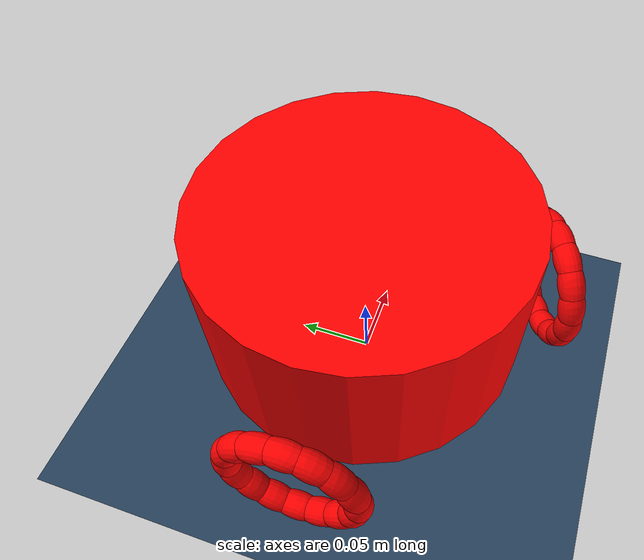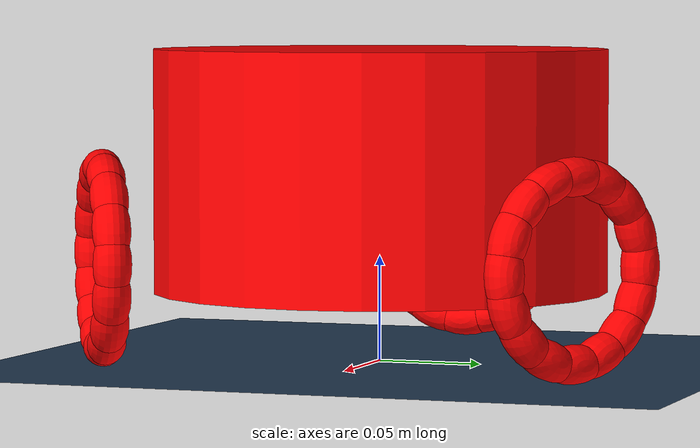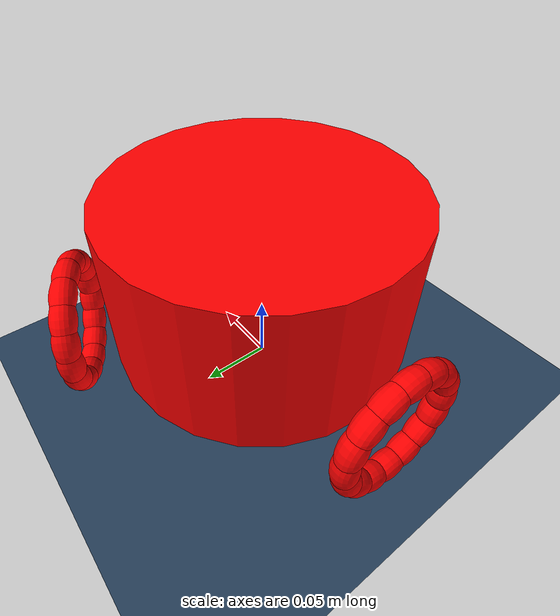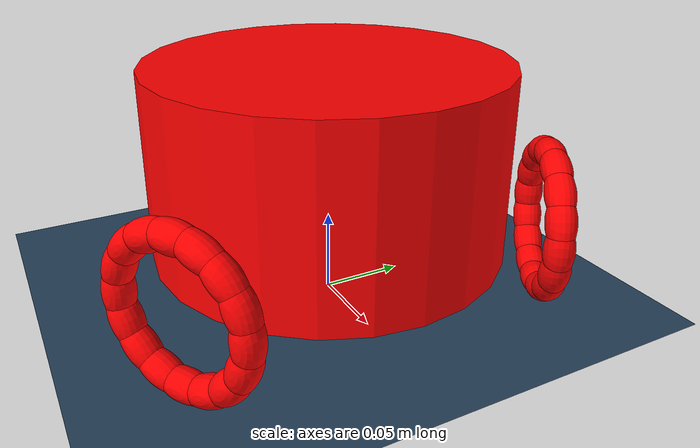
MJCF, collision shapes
<!-- Generated by lekiwi_mujoco.build_mujoco_models using MjSpec; edit sources, not this file. -->
<mujoco model="lekiwi_flat">
  <compiler angle="radian"/>

  <option integrator="implicitfast" iterations="60"/>

  <statistic extent="0.7" center="0 0 0.15"/>

  <visual>
    <global azimuth="135" elevation="-25" offwidth="1280" offheight="720"/>
    <headlight ambient="0.3 0.3 0.3" diffuse="0.6 0.6 0.6" specular="0 0 0"/>
    <rgba haze="0.15 0.25 0.35 1"/>
  </visual>

  <default>
    <default class="lekiwi_robot">
      <default class="sts3215">
        <joint armature="0.03246" damping="1.05784" frictionloss="0.195871"/>
        <general forcerange="-8.53772 8.53772" biastype="affine" gainprm="42.9119" biasprm="0 -42.9119"/>
      </default>
      <default class="lekiwi_base">
        <default class="passive_roller">
          <joint armature="1e-06" damping="2e-05" axis="0 1 0" limited="false"/>
        </default>
        <default class="roller_geom">
          <geom size="0.009 0.018 0.009" type="ellipsoid" contype="2" group="3" friction="1 0.001 1e-05" material="base_transparent"/>
        </default>
        <default class="marker">
          <geom type="mesh" contype="0" conaffinity="0" group="2"/>
        </default>
        <default class="base_visual">
          <geom type="mesh" contype="0" conaffinity="0" group="2"/>
        </default>
      </default>
    </default>
  </default>

  <asset>
    <texture type="skybox" colorspace="auto" builtin="gradient" rgb1="0.3 0.5 0.7" rgb2="0 0 0" width="512" height="3072"/>
    <texture type="2d" colorspace="auto" name="groundplane" builtin="checker" mark="edge" rgb1="0.2 0.3 0.4" rgb2="0.1 0.2 0.3" markrgb="0.8 0.8 0.8" width="300" height="300"/>
    <material name="groundplane" texture="groundplane" texrepeat="5 5" texuniform="true" reflectance="0.2"/>
    <material name="base_light_grey" rgba="0.8 0.8 0.8 1"/>
    <material name="base_charcoal" rgba="0.15 0.15 0.15 1"/>
    <material name="base_transparent" rgba="1 0 0 0.3"/>
    <mesh name="ld06_lidar" file="../../lekiwi_description/meshes/ld06_lidar.stl"/>
    <mesh name="bno055_imu" file="../../lekiwi_description/meshes/bno055_imu.stl"/>
    <mesh name="respeaker_flex_mic" file="../../lekiwi_description/meshes/respeaker_flex_mic.stl"/>
    <mesh name="lekiwi_base_visual" file="../../lekiwi_description/meshes/lekiwi_base_mujoco.stl"/>
    <mesh name="omni_wheel_visual" file="../../lekiwi_description/meshes/omni_wheel_mujoco.stl"/>
  </asset>

  <worldbody>
    <geom name="floor" size="0 0 0.05" type="plane" friction="0.4" material="groundplane"/>
    <light pos="0 0 1.5" type="directional"/>
    <frame name="lekiwi_spawn">
      <body name="base_link" childclass="lekiwi_base" pos="0 0 0.04064">
        <inertial pos="0 0 0" mass="2" diaginertia="0.01 0.01 0.02"/>
        <joint type="free"/>
        <geom name="base_link_collision" size="0.108 0.0575" pos="0 0 0.05025" type="cylinder" group="3" mass="0" material="base_transparent"/>
        <geom class="base_visual" quat="-0.707107 0 0 0.707107" mass="0" material="base_light_grey" mesh="lekiwi_base_visual"/>
        <body name="left_wheel_link" pos="0.0661195 0.114522 0.01036" quat="0.612372 -0.353553 0.612372 0.353553">
          <inertial pos="0 0 0" quat="-0.5 0.5 0.5 0.5" mass="0.068" diaginertia="0.00094096 0.000969962 0.000969962"/>
          <joint name="left_wheel_joint" class="sts3215" damping="0"/>
          <geom class="base_visual" mass="0" material="base_charcoal" mesh="omni_wheel_visual"/>
          <body name="left_roller_0" pos="0.042 0 0">
            <joint name="left_roller_joint_0" class="passive_roller"/>
            <geom name="left_roller_collision_0" class="roller_geom" mass="0.002"/>
          </body>
          <body name="left_roller_1" pos="0.0388029 0.0160727 0" quat="0.980785 0 0 0.19509">
            <joint name="left_roller_joint_1" class="passive_roller"/>
            <geom name="left_roller_collision_1" class="roller_geom" mass="0.002"/>
          </body>
          <body name="left_roller_2" pos="0.0296985 0.0296985 0" quat="0.92388 0 0 0.382683">
            <joint name="left_roller_joint_2" class="passive_roller"/>
            <geom name="left_roller_collision_2" class="roller_geom" mass="0.002"/>
          </body>
          <body name="left_roller_3" pos="0.0160727 0.0388029 0" quat="0.83147 0 0 0.55557">
            <joint name="left_roller_joint_3" class="passive_roller"/>
            <geom name="left_roller_collision_3" class="roller_geom" mass="0.002"/>
          </body>
          <body name="left_roller_4" pos="0 0.042 0" quat="0.707107 0 0 0.707107">
            <joint name="left_roller_joint_4" class="passive_roller"/>
            <geom name="left_roller_collision_4" class="roller_geom" mass="0.002"/>
          </body>
          <body name="left_roller_5" pos="-0.0160727 0.0388029 0" quat="0.55557 0 0 0.83147">
            <joint name="left_roller_joint_5" class="passive_roller"/>
            <geom name="left_roller_collision_5" class="roller_geom" mass="0.002"/>
          </body>
          <body name="left_roller_6" pos="-0.0296985 0.0296985 0" quat="0.382683 0 0 0.92388">
            <joint name="left_roller_joint_6" class="passive_roller"/>
            <geom name="left_roller_collision_6" class="roller_geom" mass="0.002"/>
          </body>
          <body name="left_roller_7" pos="-0.0388029 0.0160727 0" quat="0.19509 0 0 0.980785">
            <joint name="left_roller_joint_7" class="passive_roller"/>
            <geom name="left_roller_collision_7" class="roller_geom" mass="0.002"/>
          </body>
          <body name="left_roller_8" pos="-0.042 0 0" quat="0 0 0 1">
            <joint name="left_roller_joint_8" class="passive_roller"/>
            <geom name="left_roller_collision_8" class="roller_geom" mass="0.002"/>
          </body>
          <body name="left_roller_9" pos="-0.0388029 -0.0160727 0" quat="-0.19509 0 0 0.980785">
            <joint name="left_roller_joint_9" class="passive_roller"/>
            <geom name="left_roller_collision_9" class="roller_geom" mass="0.002"/>
          </body>
          <body name="left_roller_10" pos="-0.0296985 -0.0296985 0" quat="-0.382683 0 0 0.92388">
            <joint name="left_roller_joint_10" class="passive_roller"/>
            <geom name="left_roller_collision_10" class="roller_geom" mass="0.002"/>
          </body>
          <body name="left_roller_11" pos="-0.0160727 -0.0388029 0" quat="-0.55557 0 0 0.83147">
            <joint name="left_roller_joint_11" class="passive_roller"/>
            <geom name="left_roller_collision_11" class="roller_geom" mass="0.002"/>
          </body>
          <body name="left_roller_12" pos="0 -0.042 0" quat="-0.707107 0 0 0.707107">
            <joint name="left_roller_joint_12" class="passive_roller"/>
            <geom name="left_roller_collision_12" class="roller_geom" mass="0.002"/>
          </body>
          <body name="left_roller_13" pos="0.0160727 -0.0388029 0" quat="-0.83147 0 0 0.55557">
            <joint name="left_roller_joint_13" class="passive_roller"/>
            <geom name="left_roller_collision_13" class="roller_geom" mass="0.002"/>
          </body>
          <body name="left_roller_14" pos="0.0296985 -0.0296985 0" quat="-0.92388 0 0 0.382683">
            <joint name="left_roller_joint_14" class="passive_roller"/>
            <geom name="left_roller_collision_14" class="roller_geom" mass="0.002"/>
          </body>
          <body name="left_roller_15" pos="0.0388029 -0.0160727 0" quat="-0.980785 0 0 0.19509">
            <joint name="left_roller_joint_15" class="passive_roller"/>
            <geom name="left_roller_collision_15" class="roller_geom" mass="0.002"/>
          </body>
        </body>
        <body name="back_wheel_link" pos="-0.132239 0 0.01036" quat="0 -0.707107 0 0.707107">
          <inertial pos="0 0 0" quat="-0.5 0.5 0.5 0.5" mass="0.068" diaginertia="0.00094096 0.000969962 0.000969962"/>
          <joint name="back_wheel_joint" class="sts3215" damping="0"/>
          <geom class="base_visual" mass="0" material="base_charcoal" mesh="omni_wheel_visual"/>
          <body name="back_roller_0" pos="0.042 0 0">
            <joint name="back_roller_joint_0" class="passive_roller"/>
            <geom name="back_roller_collision_0" class="roller_geom" mass="0.002"/>
          </body>
          <body name="back_roller_1" pos="0.0388029 0.0160727 0" quat="0.980785 0 0 0.19509">
            <joint name="back_roller_joint_1" class="passive_roller"/>
            <geom name="back_roller_collision_1" class="roller_geom" mass="0.002"/>
          </body>
          <body name="back_roller_2" pos="0.0296985 0.0296985 0" quat="0.92388 0 0 0.382683">
            <joint name="back_roller_joint_2" class="passive_roller"/>
            <geom name="back_roller_collision_2" class="roller_geom" mass="0.002"/>
          </body>
          <body name="back_roller_3" pos="0.0160727 0.0388029 0" quat="0.83147 0 0 0.55557">
            <joint name="back_roller_joint_3" class="passive_roller"/>
            <geom name="back_roller_collision_3" class="roller_geom" mass="0.002"/>
          </body>
          <body name="back_roller_4" pos="0 0.042 0" quat="0.707107 0 0 0.707107">
            <joint name="back_roller_joint_4" class="passive_roller"/>
            <geom name="back_roller_collision_4" class="roller_geom" mass="0.002"/>
          </body>
          <body name="back_roller_5" pos="-0.0160727 0.0388029 0" quat="0.55557 0 0 0.83147">
            <joint name="back_roller_joint_5" class="passive_roller"/>
            <geom name="back_roller_collision_5" class="roller_geom" mass="0.002"/>
          </body>
          <body name="back_roller_6" pos="-0.0296985 0.0296985 0" quat="0.382683 0 0 0.92388">
            <joint name="back_roller_joint_6" class="passive_roller"/>
            <geom name="back_roller_collision_6" class="roller_geom" mass="0.002"/>
          </body>
          <body name="back_roller_7" pos="-0.0388029 0.0160727 0" quat="0.19509 0 0 0.980785">
            <joint name="back_roller_joint_7" class="passive_roller"/>
            <geom name="back_roller_collision_7" class="roller_geom" mass="0.002"/>
          </body>
          <body name="back_roller_8" pos="-0.042 0 0" quat="0 0 0 1">
            <joint name="back_roller_joint_8" class="passive_roller"/>
            <geom name="back_roller_collision_8" class="roller_geom" mass="0.002"/>
          </body>
          <body name="back_roller_9" pos="-0.0388029 -0.0160727 0" quat="-0.19509 0 0 0.980785">
            <joint name="back_roller_joint_9" class="passive_roller"/>
            <geom name="back_roller_collision_9" class="roller_geom" mass="0.002"/>
          </body>
          <body name="back_roller_10" pos="-0.0296985 -0.0296985 0" quat="-0.382683 0 0 0.92388">
            <joint name="back_roller_joint_10" class="passive_roller"/>
            <geom name="back_roller_collision_10" class="roller_geom" mass="0.002"/>
          </body>
          <body name="back_roller_11" pos="-0.0160727 -0.0388029 0" quat="-0.55557 0 0 0.83147">
            <joint name="back_roller_joint_11" class="passive_roller"/>
            <geom name="back_roller_collision_11" class="roller_geom" mass="0.002"/>
          </body>
          <body name="back_roller_12" pos="0 -0.042 0" quat="-0.707107 0 0 0.707107">
            <joint name="back_roller_joint_12" class="passive_roller"/>
            <geom name="back_roller_collision_12" class="roller_geom" mass="0.002"/>
          </body>
          <body name="back_roller_13" pos="0.0160727 -0.0388029 0" quat="-0.83147 0 0 0.55557">
            <joint name="back_roller_joint_13" class="passive_roller"/>
            <geom name="back_roller_collision_13" class="roller_geom" mass="0.002"/>
          </body>
          <body name="back_roller_14" pos="0.0296985 -0.0296985 0" quat="-0.92388 0 0 0.382683">
            <joint name="back_roller_joint_14" class="passive_roller"/>
            <geom name="back_roller_collision_14" class="roller_geom" mass="0.002"/>
          </body>
          <body name="back_roller_15" pos="0.0388029 -0.0160727 0" quat="-0.980785 0 0 0.19509">
            <joint name="back_roller_joint_15" class="passive_roller"/>
            <geom name="back_roller_collision_15" class="roller_geom" mass="0.002"/>
          </body>
        </body>
        <body name="right_wheel_link" pos="0.0661195 -0.114522 0.01036" quat="0.612372 0.353553 0.612372 -0.353553">
          <inertial pos="0 0 0" quat="-0.5 0.5 0.5 0.5" mass="0.068" diaginertia="0.00094096 0.000969962 0.000969962"/>
          <joint name="right_wheel_joint" class="sts3215" damping="0"/>
          <geom class="base_visual" mass="0" material="base_charcoal" mesh="omni_wheel_visual"/>
          <body name="right_roller_0" pos="0.042 0 0">
            <joint name="right_roller_joint_0" class="passive_roller"/>
            <geom name="right_roller_collision_0" class="roller_geom" mass="0.002"/>
          </body>
          <body name="right_roller_1" pos="0.0388029 0.0160727 0" quat="0.980785 0 0 0.19509">
            <joint name="right_roller_joint_1" class="passive_roller"/>
            <geom name="right_roller_collision_1" class="roller_geom" mass="0.002"/>
          </body>
          <body name="right_roller_2" pos="0.0296985 0.0296985 0" quat="0.92388 0 0 0.382683">
            <joint name="right_roller_joint_2" class="passive_roller"/>
            <geom name="right_roller_collision_2" class="roller_geom" mass="0.002"/>
          </body>
          <body name="right_roller_3" pos="0.0160727 0.0388029 0" quat="0.83147 0 0 0.55557">
            <joint name="right_roller_joint_3" class="passive_roller"/>
            <geom name="right_roller_collision_3" class="roller_geom" mass="0.002"/>
          </body>
          <body name="right_roller_4" pos="0 0.042 0" quat="0.707107 0 0 0.707107">
            <joint name="right_roller_joint_4" class="passive_roller"/>
            <geom name="right_roller_collision_4" class="roller_geom" mass="0.002"/>
          </body>
          <body name="right_roller_5" pos="-0.0160727 0.0388029 0" quat="0.55557 0 0 0.83147">
            <joint name="right_roller_joint_5" class="passive_roller"/>
            <geom name="right_roller_collision_5" class="roller_geom" mass="0.002"/>
          </body>
          <body name="right_roller_6" pos="-0.0296985 0.0296985 0" quat="0.382683 0 0 0.92388">
            <joint name="right_roller_joint_6" class="passive_roller"/>
            <geom name="right_roller_collision_6" class="roller_geom" mass="0.002"/>
          </body>
          <body name="right_roller_7" pos="-0.0388029 0.0160727 0" quat="0.19509 0 0 0.980785">
            <joint name="right_roller_joint_7" class="passive_roller"/>
            <geom name="right_roller_collision_7" class="roller_geom" mass="0.002"/>
          </body>
          <body name="right_roller_8" pos="-0.042 0 0" quat="0 0 0 1">
            <joint name="right_roller_joint_8" class="passive_roller"/>
            <geom name="right_roller_collision_8" class="roller_geom" mass="0.002"/>
          </body>
          <body name="right_roller_9" pos="-0.0388029 -0.0160727 0" quat="-0.19509 0 0 0.980785">
            <joint name="right_roller_joint_9" class="passive_roller"/>
            <geom name="right_roller_collision_9" class="roller_geom" mass="0.002"/>
          </body>
          <body name="right_roller_10" pos="-0.0296985 -0.0296985 0" quat="-0.382683 0 0 0.92388">
            <joint name="right_roller_joint_10" class="passive_roller"/>
            <geom name="right_roller_collision_10" class="roller_geom" mass="0.002"/>
          </body>
          <body name="right_roller_11" pos="-0.0160727 -0.0388029 0" quat="-0.55557 0 0 0.83147">
            <joint name="right_roller_joint_11" class="passive_roller"/>
            <geom name="right_roller_collision_11" class="roller_geom" mass="0.002"/>
          </body>
          <body name="right_roller_12" pos="0 -0.042 0" quat="-0.707107 0 0 0.707107">
            <joint name="right_roller_joint_12" class="passive_roller"/>
            <geom name="right_roller_collision_12" class="roller_geom" mass="0.002"/>
          </body>
          <body name="right_roller_13" pos="0.0160727 -0.0388029 0" quat="-0.83147 0 0 0.55557">
            <joint name="right_roller_joint_13" class="passive_roller"/>
            <geom name="right_roller_collision_13" class="roller_geom" mass="0.002"/>
          </body>
          <body name="right_roller_14" pos="0.0296985 -0.0296985 0" quat="-0.92388 0 0 0.382683">
            <joint name="right_roller_joint_14" class="passive_roller"/>
            <geom name="right_roller_collision_14" class="roller_geom" mass="0.002"/>
          </body>
          <body name="right_roller_15" pos="0.0388029 -0.0160727 0" quat="-0.980785 0 0 0.19509">
            <joint name="right_roller_joint_15" class="passive_roller"/>
            <geom name="right_roller_collision_15" class="roller_geom" mass="0.002"/>
          </body>
        </body>
        <body name="laser_link" pos="-0.045042 0 0.0915">
          <inertial pos="0 0 0" mass="0.2" diaginertia="0.0001 0.0001 0.0001"/>
          <body name="laser_frame" pos="0 0 0.027">
            <inertial pos="0 0 0" mass="0" diaginertia="0 0 0"/>
            <geom class="marker" pos="0 0 -0.027" quat="0.707107 0.707107 0 0" mass="0" material="base_charcoal" mesh="ld06_lidar"/>
            <site name="lidar-0" quat="0.707107 0 0.707107 0" group="4"/>
            <site name="lidar-1" quat="0.70708 -0.00617059 0.70708 0.00617059" group="4"/>
            <site name="lidar-2" quat="0.706999 -0.0123407 0.706999 0.0123407" group="4"/>
            <site name="lidar-3" quat="0.706864 -0.0185099 0.706864 0.0185099" group="4"/>
            <site name="lidar-4" quat="0.706676 -0.0246777 0.706676 0.0246777" group="4"/>
            <site name="lidar-5" quat="0.706434 -0.0308436 0.706434 0.0308436" group="4"/>
            <site name="lidar-6" quat="0.706138 -0.0370071 0.706138 0.0370071" group="4"/>
            <site name="lidar-7" quat="0.705788 -0.0431678 0.705788 0.0431678" group="4"/>
            <site name="lidar-8" quat="0.705384 -0.0493253 0.705384 0.0493253" group="4"/>
            <site name="lidar-9" quat="0.704927 -0.055479 0.704927 0.055479" group="4"/>
            <site name="lidar-10" quat="0.704416 -0.0616284 0.704416 0.0616284" group="4"/>
            <site name="lidar-11" quat="0.703851 -0.0677732 0.703851 0.0677732" group="4"/>
            <site name="lidar-12" quat="0.703233 -0.0739128 0.703233 0.0739128" group="4"/>
            <site name="lidar-13" quat="0.702561 -0.0800468 0.702561 0.0800468" group="4"/>
            <site name="lidar-14" quat="0.701836 -0.0861746 0.701836 0.0861746" group="4"/>
            <site name="lidar-15" quat="0.701057 -0.092296 0.701057 0.092296" group="4"/>
            <site name="lidar-16" quat="0.700225 -0.0984102 0.700225 0.0984102" group="4"/>
            <site name="lidar-17" quat="0.69934 -0.104517 0.69934 0.104517" group="4"/>
            <site name="lidar-18" quat="0.698401 -0.110616 0.698401 0.110616" group="4"/>
            <site name="lidar-19" quat="0.697409 -0.116706 0.697409 0.116706" group="4"/>
            <site name="lidar-20" quat="0.696364 -0.122788 0.696364 0.122788" group="4"/>
            <site name="lidar-21" quat="0.695266 -0.12886 0.695266 0.12886" group="4"/>
            <site name="lidar-22" quat="0.694115 -0.134922 0.694115 0.134922" group="4"/>
            <site name="lidar-23" quat="0.692911 -0.140974 0.692911 0.140974" group="4"/>
            <site name="lidar-24" quat="0.691655 -0.147016 0.691655 0.147016" group="4"/>
            <site name="lidar-25" quat="0.690346 -0.153046 0.690346 0.153046" group="4"/>
            <site name="lidar-26" quat="0.688984 -0.159064 0.688984 0.159064" group="4"/>
            <site name="lidar-27" quat="0.687569 -0.165071 0.687569 0.165071" group="4"/>
            <site name="lidar-28" quat="0.686103 -0.171065 0.686103 0.171065" group="4"/>
            <site name="lidar-29" quat="0.684584 -0.177045 0.684584 0.177045" group="4"/>
            <site name="lidar-30" quat="0.683013 -0.183013 0.683013 0.183013" group="4"/>
            <site name="lidar-31" quat="0.68139 -0.188966 0.68139 0.188966" group="4"/>
            <site name="lidar-32" quat="0.679715 -0.194905 0.679715 0.194905" group="4"/>
            <site name="lidar-33" quat="0.677988 -0.200829 0.677988 0.200829" group="4"/>
            <site name="lidar-34" quat="0.67621 -0.206738 0.67621 0.206738" group="4"/>
            <site name="lidar-35" quat="0.67438 -0.212631 0.67438 0.212631" group="4"/>
            <site name="lidar-36" quat="0.672499 -0.218508 0.672499 0.218508" group="4"/>
            <site name="lidar-37" quat="0.670566 -0.224368 0.670566 0.224368" group="4"/>
            <site name="lidar-38" quat="0.668583 -0.230211 0.668583 0.230211" group="4"/>
            <site name="lidar-39" quat="0.666548 -0.236037 0.666548 0.236037" group="4"/>
            <site name="lidar-40" quat="0.664463 -0.241845 0.664463 0.241845" group="4"/>
            <site name="lidar-41" quat="0.662327 -0.247634 0.662327 0.247634" group="4"/>
            <site name="lidar-42" quat="0.660141 -0.253404 0.660141 0.253404" group="4"/>
            <site name="lidar-43" quat="0.657905 -0.259156 0.657905 0.259156" group="4"/>
            <site name="lidar-44" quat="0.655618 -0.264887 0.655618 0.264887" group="4"/>
            <site name="lidar-45" quat="0.653281 -0.270598 0.653281 0.270598" group="4"/>
            <site name="lidar-46" quat="0.650895 -0.276289 0.650895 0.276289" group="4"/>
            <site name="lidar-47" quat="0.648459 -0.281958 0.648459 0.281958" group="4"/>
            <site name="lidar-48" quat="0.645974 -0.287606 0.645974 0.287606" group="4"/>
            <site name="lidar-49" quat="0.64344 -0.293232 0.64344 0.293232" group="4"/>
            <site name="lidar-50" quat="0.640856 -0.298836 0.640856 0.298836" group="4"/>
            <site name="lidar-51" quat="0.638224 -0.304417 0.638224 0.304417" group="4"/>
            <site name="lidar-52" quat="0.635543 -0.309975 0.635543 0.309975" group="4"/>
            <site name="lidar-53" quat="0.632814 -0.315509 0.632814 0.315509" group="4"/>
            <site name="lidar-54" quat="0.630037 -0.32102 0.630037 0.32102" group="4"/>
            <site name="lidar-55" quat="0.627211 -0.326506 0.627211 0.326506" group="4"/>
            <site name="lidar-56" quat="0.624338 -0.331967 0.624338 0.331967" group="4"/>
            <site name="lidar-57" quat="0.621418 -0.337402 0.621418 0.337402" group="4"/>
            <site name="lidar-58" quat="0.61845 -0.342812 0.61845 0.342812" group="4"/>
            <site name="lidar-59" quat="0.615434 -0.348196 0.615434 0.348196" group="4"/>
            <site name="lidar-60" quat="0.612372 -0.353553 0.612372 0.353553" group="4"/>
            <site name="lidar-61" quat="0.609264 -0.358884 0.609264 0.358884" group="4"/>
            <site name="lidar-62" quat="0.606109 -0.364187 0.606109 0.364187" group="4"/>
            <site name="lidar-63" quat="0.602908 -0.369462 0.602908 0.369462" group="4"/>
            <site name="lidar-64" quat="0.599661 -0.37471 0.599661 0.37471" group="4"/>
            <site name="lidar-65" quat="0.596368 -0.379928 0.596368 0.379928" group="4"/>
            <site name="lidar-66" quat="0.59303 -0.385118 0.59303 0.385118" group="4"/>
            <site name="lidar-67" quat="0.589646 -0.390278 0.589646 0.390278" group="4"/>
            <site name="lidar-68" quat="0.586218 -0.395409 0.586218 0.395409" group="4"/>
            <site name="lidar-69" quat="0.582745 -0.40051 0.582745 0.40051" group="4"/>
            <site name="lidar-70" quat="0.579228 -0.40558 0.579228 0.40558" group="4"/>
            <site name="lidar-71" quat="0.575667 -0.410619 0.575667 0.410619" group="4"/>
            <site name="lidar-72" quat="0.572061 -0.415627 0.572061 0.415627" group="4"/>
            <site name="lidar-73" quat="0.568413 -0.420603 0.568413 0.420603" group="4"/>
            <site name="lidar-74" quat="0.564721 -0.425547 0.564721 0.425547" group="4"/>
            <site name="lidar-75" quat="0.560986 -0.430459 0.560986 0.430459" group="4"/>
            <site name="lidar-76" quat="0.557208 -0.435338 0.557208 0.435338" group="4"/>
            <site name="lidar-77" quat="0.553388 -0.440184 0.553388 0.440184" group="4"/>
            <site name="lidar-78" quat="0.549525 -0.444997 0.549525 0.444997" group="4"/>
            <site name="lidar-79" quat="0.545621 -0.449775 0.545621 0.449775" group="4"/>
            <site name="lidar-80" quat="0.541675 -0.454519 0.541675 0.454519" group="4"/>
            <site name="lidar-81" quat="0.537688 -0.459229 0.537688 0.459229" group="4"/>
            <site name="lidar-82" quat="0.53366 -0.463904 0.53366 0.463904" group="4"/>
            <site name="lidar-83" quat="0.529592 -0.468543 0.529592 0.468543" group="4"/>
            <site name="lidar-84" quat="0.525483 -0.473147 0.525483 0.473147" group="4"/>
            <site name="lidar-85" quat="0.521334 -0.477714 0.521334 0.477714" group="4"/>
            <site name="lidar-86" quat="0.517145 -0.482246 0.517145 0.482246" group="4"/>
            <site name="lidar-87" quat="0.512917 -0.48674 0.512917 0.48674" group="4"/>
            <site name="lidar-88" quat="0.50865 -0.491198 0.50865 0.491198" group="4"/>
            <site name="lidar-89" quat="0.504344 -0.495618 0.504344 0.495618" group="4"/>
            <site name="lidar-90" quat="0.5 -0.5 0.5 0.5" group="4"/>
            <site name="lidar-91" quat="0.495618 -0.504344 0.495618 0.504344" group="4"/>
            <site name="lidar-92" quat="0.491198 -0.50865 0.491198 0.50865" group="4"/>
            <site name="lidar-93" quat="0.48674 -0.512917 0.48674 0.512917" group="4"/>
            <site name="lidar-94" quat="0.482246 -0.517145 0.482246 0.517145" group="4"/>
            <site name="lidar-95" quat="0.477714 -0.521334 0.477714 0.521334" group="4"/>
            <site name="lidar-96" quat="0.473147 -0.525483 0.473147 0.525483" group="4"/>
            <site name="lidar-97" quat="0.468543 -0.529592 0.468543 0.529592" group="4"/>
            <site name="lidar-98" quat="0.463904 -0.53366 0.463904 0.53366" group="4"/>
            <site name="lidar-99" quat="0.459229 -0.537688 0.459229 0.537688" group="4"/>
            <site name="lidar-100" quat="0.454519 -0.541675 0.454519 0.541675" group="4"/>
            <site name="lidar-101" quat="0.449775 -0.545621 0.449775 0.545621" group="4"/>
            <site name="lidar-102" quat="0.444997 -0.549525 0.444997 0.549525" group="4"/>
            <site name="lidar-103" quat="0.440184 -0.553388 0.440184 0.553388" group="4"/>
            <site name="lidar-104" quat="0.435338 -0.557208 0.435338 0.557208" group="4"/>
            <site name="lidar-105" quat="0.430459 -0.560986 0.430459 0.560986" group="4"/>
            <site name="lidar-106" quat="0.425547 -0.564721 0.425547 0.564721" group="4"/>
            <site name="lidar-107" quat="0.420603 -0.568413 0.420603 0.568413" group="4"/>
            <site name="lidar-108" quat="0.415627 -0.572061 0.415627 0.572061" group="4"/>
            <site name="lidar-109" quat="0.410619 -0.575667 0.410619 0.575667" group="4"/>
            <site name="lidar-110" quat="0.40558 -0.579228 0.40558 0.579228" group="4"/>
            <site name="lidar-111" quat="0.40051 -0.582745 0.40051 0.582745" group="4"/>
            <site name="lidar-112" quat="0.395409 -0.586218 0.395409 0.586218" group="4"/>
            <site name="lidar-113" quat="0.390278 -0.589646 0.390278 0.589646" group="4"/>
            <site name="lidar-114" quat="0.385118 -0.59303 0.385118 0.59303" group="4"/>
            <site name="lidar-115" quat="0.379928 -0.596368 0.379928 0.596368" group="4"/>
            <site name="lidar-116" quat="0.37471 -0.599661 0.37471 0.599661" group="4"/>
            <site name="lidar-117" quat="0.369462 -0.602908 0.369462 0.602908" group="4"/>
            <site name="lidar-118" quat="0.364187 -0.606109 0.364187 0.606109" group="4"/>
            <site name="lidar-119" quat="0.358884 -0.609264 0.358884 0.609264" group="4"/>
            <site name="lidar-120" quat="0.353553 -0.612372 0.353553 0.612372" group="4"/>
            <site name="lidar-121" quat="0.348196 -0.615434 0.348196 0.615434" group="4"/>
            <site name="lidar-122" quat="0.342812 -0.61845 0.342812 0.61845" group="4"/>
            <site name="lidar-123" quat="0.337402 -0.621418 0.337402 0.621418" group="4"/>
            <site name="lidar-124" quat="0.331967 -0.624338 0.331967 0.624338" group="4"/>
            <site name="lidar-125" quat="0.326506 -0.627211 0.326506 0.627211" group="4"/>
            <site name="lidar-126" quat="0.32102 -0.630037 0.32102 0.630037" group="4"/>
            <site name="lidar-127" quat="0.315509 -0.632814 0.315509 0.632814" group="4"/>
            <site name="lidar-128" quat="0.309975 -0.635543 0.309975 0.635543" group="4"/>
            <site name="lidar-129" quat="0.304417 -0.638224 0.304417 0.638224" group="4"/>
            <site name="lidar-130" quat="0.298836 -0.640856 0.298836 0.640856" group="4"/>
            <site name="lidar-131" quat="0.293232 -0.64344 0.293232 0.64344" group="4"/>
            <site name="lidar-132" quat="0.287606 -0.645974 0.287606 0.645974" group="4"/>
            <site name="lidar-133" quat="0.281958 -0.648459 0.281958 0.648459" group="4"/>
            <site name="lidar-134" quat="0.276289 -0.650895 0.276289 0.650895" group="4"/>
            <site name="lidar-135" quat="0.270598 -0.653281 0.270598 0.653281" group="4"/>
            <site name="lidar-136" quat="0.264887 -0.655618 0.264887 0.655618" group="4"/>
            <site name="lidar-137" quat="0.259156 -0.657905 0.259156 0.657905" group="4"/>
            <site name="lidar-138" quat="0.253404 -0.660141 0.253404 0.660141" group="4"/>
            <site name="lidar-139" quat="0.247634 -0.662327 0.247634 0.662327" group="4"/>
            <site name="lidar-140" quat="0.241845 -0.664463 0.241845 0.664463" group="4"/>
            <site name="lidar-141" quat="0.236037 -0.666548 0.236037 0.666548" group="4"/>
            <site name="lidar-142" quat="0.230211 -0.668583 0.230211 0.668583" group="4"/>
            <site name="lidar-143" quat="0.224368 -0.670566 0.224368 0.670566" group="4"/>
            <site name="lidar-144" quat="0.218508 -0.672499 0.218508 0.672499" group="4"/>
            <site name="lidar-145" quat="0.212631 -0.67438 0.212631 0.67438" group="4"/>
            <site name="lidar-146" quat="0.206738 -0.67621 0.206738 0.67621" group="4"/>
            <site name="lidar-147" quat="0.200829 -0.677988 0.200829 0.677988" group="4"/>
            <site name="lidar-148" quat="0.194905 -0.679715 0.194905 0.679715" group="4"/>
            <site name="lidar-149" quat="0.188966 -0.68139 0.188966 0.68139" group="4"/>
            <site name="lidar-150" quat="0.183013 -0.683013 0.183013 0.683013" group="4"/>
            <site name="lidar-151" quat="0.177045 -0.684584 0.177045 0.684584" group="4"/>
            <site name="lidar-152" quat="0.171065 -0.686103 0.171065 0.686103" group="4"/>
            <site name="lidar-153" quat="0.165071 -0.687569 0.165071 0.687569" group="4"/>
            <site name="lidar-154" quat="0.159064 -0.688984 0.159064 0.688984" group="4"/>
            <site name="lidar-155" quat="0.153046 -0.690346 0.153046 0.690346" group="4"/>
            <site name="lidar-156" quat="0.147016 -0.691655 0.147016 0.691655" group="4"/>
            <site name="lidar-157" quat="0.140974 -0.692911 0.140974 0.692911" group="4"/>
            <site name="lidar-158" quat="0.134922 -0.694115 0.134922 0.694115" group="4"/>
            <site name="lidar-159" quat="0.12886 -0.695266 0.12886 0.695266" group="4"/>
            <site name="lidar-160" quat="0.122788 -0.696364 0.122788 0.696364" group="4"/>
            <site name="lidar-161" quat="0.116706 -0.697409 0.116706 0.697409" group="4"/>
            <site name="lidar-162" quat="0.110616 -0.698401 0.110616 0.698401" group="4"/>
            <site name="lidar-163" quat="0.104517 -0.69934 0.104517 0.69934" group="4"/>
            <site name="lidar-164" quat="0.0984102 -0.700225 0.0984102 0.700225" group="4"/>
            <site name="lidar-165" quat="0.092296 -0.701057 0.092296 0.701057" group="4"/>
            <site name="lidar-166" quat="0.0861746 -0.701836 0.0861746 0.701836" group="4"/>
            <site name="lidar-167" quat="0.0800468 -0.702561 0.0800468 0.702561" group="4"/>
            <site name="lidar-168" quat="0.0739128 -0.703233 0.0739128 0.703233" group="4"/>
            <site name="lidar-169" quat="0.0677732 -0.703851 0.0677732 0.703851" group="4"/>
            <site name="lidar-170" quat="0.0616284 -0.704416 0.0616284 0.704416" group="4"/>
            <site name="lidar-171" quat="0.055479 -0.704927 0.055479 0.704927" group="4"/>
            <site name="lidar-172" quat="0.0493253 -0.705384 0.0493253 0.705384" group="4"/>
            <site name="lidar-173" quat="0.0431678 -0.705788 0.0431678 0.705788" group="4"/>
            <site name="lidar-174" quat="0.0370071 -0.706138 0.0370071 0.706138" group="4"/>
            <site name="lidar-175" quat="0.0308436 -0.706434 0.0308436 0.706434" group="4"/>
            <site name="lidar-176" quat="0.0246777 -0.706676 0.0246777 0.706676" group="4"/>
            <site name="lidar-177" quat="0.0185099 -0.706864 0.0185099 0.706864" group="4"/>
            <site name="lidar-178" quat="0.0123407 -0.706999 0.0123407 0.706999" group="4"/>
            <site name="lidar-179" quat="0.00617059 -0.70708 0.00617059 0.70708" group="4"/>
            <site name="lidar-180" quat="0 -0.707107 0 0.707107" group="4"/>
            <site name="lidar-181" quat="-0.00617059 -0.70708 -0.00617059 0.70708" group="4"/>
            <site name="lidar-182" quat="-0.0123407 -0.706999 -0.0123407 0.706999" group="4"/>
            <site name="lidar-183" quat="-0.0185099 -0.706864 -0.0185099 0.706864" group="4"/>
            <site name="lidar-184" quat="-0.0246777 -0.706676 -0.0246777 0.706676" group="4"/>
            <site name="lidar-185" quat="-0.0308436 -0.706434 -0.0308436 0.706434" group="4"/>
            <site name="lidar-186" quat="-0.0370071 -0.706138 -0.0370071 0.706138" group="4"/>
            <site name="lidar-187" quat="-0.0431678 -0.705788 -0.0431678 0.705788" group="4"/>
            <site name="lidar-188" quat="-0.0493253 -0.705384 -0.0493253 0.705384" group="4"/>
            <site name="lidar-189" quat="-0.055479 -0.704927 -0.055479 0.704927" group="4"/>
            <site name="lidar-190" quat="-0.0616284 -0.704416 -0.0616284 0.704416" group="4"/>
            <site name="lidar-191" quat="-0.0677732 -0.703851 -0.0677732 0.703851" group="4"/>
            <site name="lidar-192" quat="-0.0739128 -0.703233 -0.0739128 0.703233" group="4"/>
            <site name="lidar-193" quat="-0.0800468 -0.702561 -0.0800468 0.702561" group="4"/>
            <site name="lidar-194" quat="-0.0861746 -0.701836 -0.0861746 0.701836" group="4"/>
            <site name="lidar-195" quat="-0.092296 -0.701057 -0.092296 0.701057" group="4"/>
            <site name="lidar-196" quat="-0.0984102 -0.700225 -0.0984102 0.700225" group="4"/>
            <site name="lidar-197" quat="-0.104517 -0.69934 -0.104517 0.69934" group="4"/>
            <site name="lidar-198" quat="-0.110616 -0.698401 -0.110616 0.698401" group="4"/>
            <site name="lidar-199" quat="-0.116706 -0.697409 -0.116706 0.697409" group="4"/>
            <site name="lidar-200" quat="-0.122788 -0.696364 -0.122788 0.696364" group="4"/>
            <site name="lidar-201" quat="-0.12886 -0.695266 -0.12886 0.695266" group="4"/>
            <site name="lidar-202" quat="-0.134922 -0.694115 -0.134922 0.694115" group="4"/>
            <site name="lidar-203" quat="-0.140974 -0.692911 -0.140974 0.692911" group="4"/>
            <site name="lidar-204" quat="-0.147016 -0.691655 -0.147016 0.691655" group="4"/>
            <site name="lidar-205" quat="-0.153046 -0.690346 -0.153046 0.690346" group="4"/>
            <site name="lidar-206" quat="-0.159064 -0.688984 -0.159064 0.688984" group="4"/>
            <site name="lidar-207" quat="-0.165071 -0.687569 -0.165071 0.687569" group="4"/>
            <site name="lidar-208" quat="-0.171065 -0.686103 -0.171065 0.686103" group="4"/>
            <site name="lidar-209" quat="-0.177045 -0.684584 -0.177045 0.684584" group="4"/>
            <site name="lidar-210" quat="-0.183013 -0.683013 -0.183013 0.683013" group="4"/>
            <site name="lidar-211" quat="-0.188966 -0.68139 -0.188966 0.68139" group="4"/>
            <site name="lidar-212" quat="-0.194905 -0.679715 -0.194905 0.679715" group="4"/>
            <site name="lidar-213" quat="-0.200829 -0.677988 -0.200829 0.677988" group="4"/>
            <site name="lidar-214" quat="-0.206738 -0.67621 -0.206738 0.67621" group="4"/>
            <site name="lidar-215" quat="-0.212631 -0.67438 -0.212631 0.67438" group="4"/>
            <site name="lidar-216" quat="-0.218508 -0.672499 -0.218508 0.672499" group="4"/>
            <site name="lidar-217" quat="-0.224368 -0.670566 -0.224368 0.670566" group="4"/>
            <site name="lidar-218" quat="-0.230211 -0.668583 -0.230211 0.668583" group="4"/>
            <site name="lidar-219" quat="-0.236037 -0.666548 -0.236037 0.666548" group="4"/>
            <site name="lidar-220" quat="-0.241845 -0.664463 -0.241845 0.664463" group="4"/>
            <site name="lidar-221" quat="-0.247634 -0.662327 -0.247634 0.662327" group="4"/>
            <site name="lidar-222" quat="-0.253404 -0.660141 -0.253404 0.660141" group="4"/>
            <site name="lidar-223" quat="-0.259156 -0.657905 -0.259156 0.657905" group="4"/>
            <site name="lidar-224" quat="-0.264887 -0.655618 -0.264887 0.655618" group="4"/>
            <site name="lidar-225" quat="-0.270598 -0.653281 -0.270598 0.653281" group="4"/>
            <site name="lidar-226" quat="-0.276289 -0.650895 -0.276289 0.650895" group="4"/>
            <site name="lidar-227" quat="-0.281958 -0.648459 -0.281958 0.648459" group="4"/>
            <site name="lidar-228" quat="-0.287606 -0.645974 -0.287606 0.645974" group="4"/>
            <site name="lidar-229" quat="-0.293232 -0.64344 -0.293232 0.64344" group="4"/>
            <site name="lidar-230" quat="-0.298836 -0.640856 -0.298836 0.640856" group="4"/>
            <site name="lidar-231" quat="-0.304417 -0.638224 -0.304417 0.638224" group="4"/>
            <site name="lidar-232" quat="-0.309975 -0.635543 -0.309975 0.635543" group="4"/>
            <site name="lidar-233" quat="-0.315509 -0.632814 -0.315509 0.632814" group="4"/>
            <site name="lidar-234" quat="-0.32102 -0.630037 -0.32102 0.630037" group="4"/>
            <site name="lidar-235" quat="-0.326506 -0.627211 -0.326506 0.627211" group="4"/>
            <site name="lidar-236" quat="-0.331967 -0.624338 -0.331967 0.624338" group="4"/>
            <site name="lidar-237" quat="-0.337402 -0.621418 -0.337402 0.621418" group="4"/>
            <site name="lidar-238" quat="-0.342812 -0.61845 -0.342812 0.61845" group="4"/>
            <site name="lidar-239" quat="-0.348196 -0.615434 -0.348196 0.615434" group="4"/>
            <site name="lidar-240" quat="-0.353553 -0.612372 -0.353553 0.612372" group="4"/>
            <site name="lidar-241" quat="-0.358884 -0.609264 -0.358884 0.609264" group="4"/>
            <site name="lidar-242" quat="-0.364187 -0.606109 -0.364187 0.606109" group="4"/>
            <site name="lidar-243" quat="-0.369462 -0.602908 -0.369462 0.602908" group="4"/>
            <site name="lidar-244" quat="-0.37471 -0.599661 -0.37471 0.599661" group="4"/>
            <site name="lidar-245" quat="-0.379928 -0.596368 -0.379928 0.596368" group="4"/>
            <site name="lidar-246" quat="-0.385118 -0.59303 -0.385118 0.59303" group="4"/>
            <site name="lidar-247" quat="-0.390278 -0.589646 -0.390278 0.589646" group="4"/>
            <site name="lidar-248" quat="-0.395409 -0.586218 -0.395409 0.586218" group="4"/>
            <site name="lidar-249" quat="-0.40051 -0.582745 -0.40051 0.582745" group="4"/>
            <site name="lidar-250" quat="-0.40558 -0.579228 -0.40558 0.579228" group="4"/>
            <site name="lidar-251" quat="-0.410619 -0.575667 -0.410619 0.575667" group="4"/>
            <site name="lidar-252" quat="-0.415627 -0.572061 -0.415627 0.572061" group="4"/>
            <site name="lidar-253" quat="-0.420603 -0.568413 -0.420603 0.568413" group="4"/>
            <site name="lidar-254" quat="-0.425547 -0.564721 -0.425547 0.564721" group="4"/>
            <site name="lidar-255" quat="-0.430459 -0.560986 -0.430459 0.560986" group="4"/>
            <site name="lidar-256" quat="-0.435338 -0.557208 -0.435338 0.557208" group="4"/>
            <site name="lidar-257" quat="-0.440184 -0.553388 -0.440184 0.553388" group="4"/>
            <site name="lidar-258" quat="-0.444997 -0.549525 -0.444997 0.549525" group="4"/>
            <site name="lidar-259" quat="-0.449775 -0.545621 -0.449775 0.545621" group="4"/>
            <site name="lidar-260" quat="-0.454519 -0.541675 -0.454519 0.541675" group="4"/>
            <site name="lidar-261" quat="-0.459229 -0.537688 -0.459229 0.537688" group="4"/>
            <site name="lidar-262" quat="-0.463904 -0.53366 -0.463904 0.53366" group="4"/>
            <site name="lidar-263" quat="-0.468543 -0.529592 -0.468543 0.529592" group="4"/>
            <site name="lidar-264" quat="-0.473147 -0.525483 -0.473147 0.525483" group="4"/>
            <site name="lidar-265" quat="-0.477714 -0.521334 -0.477714 0.521334" group="4"/>
            <site name="lidar-266" quat="-0.482246 -0.517145 -0.482246 0.517145" group="4"/>
            <site name="lidar-267" quat="-0.48674 -0.512917 -0.48674 0.512917" group="4"/>
            <site name="lidar-268" quat="-0.491198 -0.50865 -0.491198 0.50865" group="4"/>
            <site name="lidar-269" quat="-0.495618 -0.504344 -0.495618 0.504344" group="4"/>
            <site name="lidar-270" quat="-0.5 -0.5 -0.5 0.5" group="4"/>
            <site name="lidar-271" quat="-0.504344 -0.495618 -0.504344 0.495618" group="4"/>
            <site name="lidar-272" quat="-0.50865 -0.491198 -0.50865 0.491198" group="4"/>
            <site name="lidar-273" quat="-0.512917 -0.48674 -0.512917 0.48674" group="4"/>
            <site name="lidar-274" quat="-0.517145 -0.482246 -0.517145 0.482246" group="4"/>
            <site name="lidar-275" quat="-0.521334 -0.477714 -0.521334 0.477714" group="4"/>
            <site name="lidar-276" quat="-0.525483 -0.473147 -0.525483 0.473147" group="4"/>
            <site name="lidar-277" quat="-0.529592 -0.468543 -0.529592 0.468543" group="4"/>
            <site name="lidar-278" quat="-0.53366 -0.463904 -0.53366 0.463904" group="4"/>
            <site name="lidar-279" quat="-0.537688 -0.459229 -0.537688 0.459229" group="4"/>
            <site name="lidar-280" quat="-0.541675 -0.454519 -0.541675 0.454519" group="4"/>
            <site name="lidar-281" quat="-0.545621 -0.449775 -0.545621 0.449775" group="4"/>
            <site name="lidar-282" quat="-0.549525 -0.444997 -0.549525 0.444997" group="4"/>
            <site name="lidar-283" quat="-0.553388 -0.440184 -0.553388 0.440184" group="4"/>
            <site name="lidar-284" quat="-0.557208 -0.435338 -0.557208 0.435338" group="4"/>
            <site name="lidar-285" quat="-0.560986 -0.430459 -0.560986 0.430459" group="4"/>
            <site name="lidar-286" quat="-0.564721 -0.425547 -0.564721 0.425547" group="4"/>
            <site name="lidar-287" quat="-0.568413 -0.420603 -0.568413 0.420603" group="4"/>
            <site name="lidar-288" quat="-0.572061 -0.415627 -0.572061 0.415627" group="4"/>
            <site name="lidar-289" quat="-0.575667 -0.410619 -0.575667 0.410619" group="4"/>
            <site name="lidar-290" quat="-0.579228 -0.40558 -0.579228 0.40558" group="4"/>
            <site name="lidar-291" quat="-0.582745 -0.40051 -0.582745 0.40051" group="4"/>
            <site name="lidar-292" quat="-0.586218 -0.395409 -0.586218 0.395409" group="4"/>
            <site name="lidar-293" quat="-0.589646 -0.390278 -0.589646 0.390278" group="4"/>
            <site name="lidar-294" quat="-0.59303 -0.385118 -0.59303 0.385118" group="4"/>
            <site name="lidar-295" quat="-0.596368 -0.379928 -0.596368 0.379928" group="4"/>
            <site name="lidar-296" quat="-0.599661 -0.37471 -0.599661 0.37471" group="4"/>
            <site name="lidar-297" quat="-0.602908 -0.369462 -0.602908 0.369462" group="4"/>
            <site name="lidar-298" quat="-0.606109 -0.364187 -0.606109 0.364187" group="4"/>
            <site name="lidar-299" quat="-0.609264 -0.358884 -0.609264 0.358884" group="4"/>
            <site name="lidar-300" quat="-0.612372 -0.353553 -0.612372 0.353553" group="4"/>
            <site name="lidar-301" quat="-0.615434 -0.348196 -0.615434 0.348196" group="4"/>
            <site name="lidar-302" quat="-0.61845 -0.342812 -0.61845 0.342812" group="4"/>
            <site name="lidar-303" quat="-0.621418 -0.337402 -0.621418 0.337402" group="4"/>
            <site name="lidar-304" quat="-0.624338 -0.331967 -0.624338 0.331967" group="4"/>
            <site name="lidar-305" quat="-0.627211 -0.326506 -0.627211 0.326506" group="4"/>
            <site name="lidar-306" quat="-0.630037 -0.32102 -0.630037 0.32102" group="4"/>
            <site name="lidar-307" quat="-0.632814 -0.315509 -0.632814 0.315509" group="4"/>
            <site name="lidar-308" quat="-0.635543 -0.309975 -0.635543 0.309975" group="4"/>
            <site name="lidar-309" quat="-0.638224 -0.304417 -0.638224 0.304417" group="4"/>
            <site name="lidar-310" quat="-0.640856 -0.298836 -0.640856 0.298836" group="4"/>
            <site name="lidar-311" quat="-0.64344 -0.293232 -0.64344 0.293232" group="4"/>
            <site name="lidar-312" quat="-0.645974 -0.287606 -0.645974 0.287606" group="4"/>
            <site name="lidar-313" quat="-0.648459 -0.281958 -0.648459 0.281958" group="4"/>
            <site name="lidar-314" quat="-0.650895 -0.276289 -0.650895 0.276289" group="4"/>
            <site name="lidar-315" quat="-0.653281 -0.270598 -0.653281 0.270598" group="4"/>
            <site name="lidar-316" quat="-0.655618 -0.264887 -0.655618 0.264887" group="4"/>
            <site name="lidar-317" quat="-0.657905 -0.259156 -0.657905 0.259156" group="4"/>
            <site name="lidar-318" quat="-0.660141 -0.253404 -0.660141 0.253404" group="4"/>
            <site name="lidar-319" quat="-0.662327 -0.247634 -0.662327 0.247634" group="4"/>
            <site name="lidar-320" quat="-0.664463 -0.241845 -0.664463 0.241845" group="4"/>
            <site name="lidar-321" quat="-0.666548 -0.236037 -0.666548 0.236037" group="4"/>
            <site name="lidar-322" quat="-0.668583 -0.230211 -0.668583 0.230211" group="4"/>
            <site name="lidar-323" quat="-0.670566 -0.224368 -0.670566 0.224368" group="4"/>
            <site name="lidar-324" quat="-0.672499 -0.218508 -0.672499 0.218508" group="4"/>
            <site name="lidar-325" quat="-0.67438 -0.212631 -0.67438 0.212631" group="4"/>
            <site name="lidar-326" quat="-0.67621 -0.206738 -0.67621 0.206738" group="4"/>
            <site name="lidar-327" quat="-0.677988 -0.200829 -0.677988 0.200829" group="4"/>
            <site name="lidar-328" quat="-0.679715 -0.194905 -0.679715 0.194905" group="4"/>
            <site name="lidar-329" quat="-0.68139 -0.188966 -0.68139 0.188966" group="4"/>
            <site name="lidar-330" quat="-0.683013 -0.183013 -0.683013 0.183013" group="4"/>
            <site name="lidar-331" quat="-0.684584 -0.177045 -0.684584 0.177045" group="4"/>
            <site name="lidar-332" quat="-0.686103 -0.171065 -0.686103 0.171065" group="4"/>
            <site name="lidar-333" quat="-0.687569 -0.165071 -0.687569 0.165071" group="4"/>
            <site name="lidar-334" quat="-0.688984 -0.159064 -0.688984 0.159064" group="4"/>
            <site name="lidar-335" quat="-0.690346 -0.153046 -0.690346 0.153046" group="4"/>
            <site name="lidar-336" quat="-0.691655 -0.147016 -0.691655 0.147016" group="4"/>
            <site name="lidar-337" quat="-0.692911 -0.140974 -0.692911 0.140974" group="4"/>
            <site name="lidar-338" quat="-0.694115 -0.134922 -0.694115 0.134922" group="4"/>
            <site name="lidar-339" quat="-0.695266 -0.12886 -0.695266 0.12886" group="4"/>
            <site name="lidar-340" quat="-0.696364 -0.122788 -0.696364 0.122788" group="4"/>
            <site name="lidar-341" quat="-0.697409 -0.116706 -0.697409 0.116706" group="4"/>
            <site name="lidar-342" quat="-0.698401 -0.110616 -0.698401 0.110616" group="4"/>
            <site name="lidar-343" quat="-0.69934 -0.104517 -0.69934 0.104517" group="4"/>
            <site name="lidar-344" quat="-0.700225 -0.0984102 -0.700225 0.0984102" group="4"/>
            <site name="lidar-345" quat="-0.701057 -0.092296 -0.701057 0.092296" group="4"/>
            <site name="lidar-346" quat="-0.701836 -0.0861746 -0.701836 0.0861746" group="4"/>
            <site name="lidar-347" quat="-0.702561 -0.0800468 -0.702561 0.0800468" group="4"/>
            <site name="lidar-348" quat="-0.703233 -0.0739128 -0.703233 0.0739128" group="4"/>
            <site name="lidar-349" quat="-0.703851 -0.0677732 -0.703851 0.0677732" group="4"/>
            <site name="lidar-350" quat="-0.704416 -0.0616284 -0.704416 0.0616284" group="4"/>
            <site name="lidar-351" quat="-0.704927 -0.055479 -0.704927 0.055479" group="4"/>
            <site name="lidar-352" quat="-0.705384 -0.0493253 -0.705384 0.0493253" group="4"/>
            <site name="lidar-353" quat="-0.705788 -0.0431678 -0.705788 0.0431678" group="4"/>
            <site name="lidar-354" quat="-0.706138 -0.0370071 -0.706138 0.0370071" group="4"/>
            <site name="lidar-355" quat="-0.706434 -0.0308436 -0.706434 0.0308436" group="4"/>
            <site name="lidar-356" quat="-0.706676 -0.0246777 -0.706676 0.0246777" group="4"/>
            <site name="lidar-357" quat="-0.706864 -0.0185099 -0.706864 0.0185099" group="4"/>
            <site name="lidar-358" quat="-0.706999 -0.0123407 -0.706999 0.0123407" group="4"/>
            <site name="lidar-359" quat="-0.70708 -0.00617059 -0.70708 0.00617059" group="4"/>
          </body>
        </body>
        <body name="imu_link" pos="-0.044 0 0.08">
          <inertial pos="0 0 0" mass="0.01" diaginertia="1e-05 1e-05 1e-05"/>
          <geom class="marker" mass="0" material="base_charcoal" mesh="bno055_imu"/>
          <body name="imu_frame">
            <inertial pos="0 0 0" mass="0" diaginertia="0 0 0"/>
            <site name="imu_site" group="4"/>
          </body>
        </body>
        <body name="mic_link" pos="-0.045042 0 0.10901">
          <inertial pos="0 0 0" mass="0.05" diaginertia="1e-05 1e-05 1e-05"/>
          <geom class="marker" mass="0" material="base_charcoal" mesh="respeaker_flex_mic"/>
        </body>
      </body>
    </frame>
  </worldbody>

  <contact>
    <exclude body1="base_link" body2="left_wheel_link"/>
    <exclude body1="base_link" body2="back_wheel_link"/>
    <exclude body1="base_link" body2="right_wheel_link"/>
  </contact>

  <actuator>
    <general name="left_wheel_joint" joint="left_wheel_joint" ctrlrange="-4.4332 4.4332" ctrllimited="true" forcelimited="true" forcerange="-2.942 2.942" biastype="affine" gainprm="5" biasprm="0 0 -5"/>
    <general name="back_wheel_joint" joint="back_wheel_joint" ctrlrange="-4.4332 4.4332" ctrllimited="true" forcelimited="true" forcerange="-2.942 2.942" biastype="affine" gainprm="5" biasprm="0 0 -5"/>
    <general name="right_wheel_joint" joint="right_wheel_joint" ctrlrange="-4.4332 4.4332" ctrllimited="true" forcelimited="true" forcerange="-2.942 2.942" biastype="affine" gainprm="5" biasprm="0 0 -5"/>
  </actuator>

  <sensor>
    <framequat objtype="site" objname="imu_site" name="bno055_quat"/>
    <gyro site="imu_site" name="bno055_gyro"/>
    <accelerometer site="imu_site" name="bno055_accel"/>
    <rangefinder site="lidar-0" name="lidar-0" cutoff="12"/>
    <rangefinder site="lidar-1" name="lidar-1" cutoff="12"/>
    <rangefinder site="lidar-2" name="lidar-2" cutoff="12"/>
    <rangefinder site="lidar-3" name="lidar-3" cutoff="12"/>
    <rangefinder site="lidar-4" name="lidar-4" cutoff="12"/>
    <rangefinder site="lidar-5" name="lidar-5" cutoff="12"/>
    <rangefinder site="lidar-6" name="lidar-6" cutoff="12"/>
    <rangefinder site="lidar-7" name="lidar-7" cutoff="12"/>
    <rangefinder site="lidar-8" name="lidar-8" cutoff="12"/>
    <rangefinder site="lidar-9" name="lidar-9" cutoff="12"/>
    <rangefinder site="lidar-10" name="lidar-10" cutoff="12"/>
    <rangefinder site="lidar-11" name="lidar-11" cutoff="12"/>
    <rangefinder site="lidar-12" name="lidar-12" cutoff="12"/>
    <rangefinder site="lidar-13" name="lidar-13" cutoff="12"/>
    <rangefinder site="lidar-14" name="lidar-14" cutoff="12"/>
    <rangefinder site="lidar-15" name="lidar-15" cutoff="12"/>
    <rangefinder site="lidar-16" name="lidar-16" cutoff="12"/>
    <rangefinder site="lidar-17" name="lidar-17" cutoff="12"/>
    <rangefinder site="lidar-18" name="lidar-18" cutoff="12"/>
    <rangefinder site="lidar-19" name="lidar-19" cutoff="12"/>
    <rangefinder site="lidar-20" name="lidar-20" cutoff="12"/>
    <rangefinder site="lidar-21" name="lidar-21" cutoff="12"/>
    <rangefinder site="lidar-22" name="lidar-22" cutoff="12"/>
    <rangefinder site="lidar-23" name="lidar-23" cutoff="12"/>
    <rangefinder site="lidar-24" name="lidar-24" cutoff="12"/>
    <rangefinder site="lidar-25" name="lidar-25" cutoff="12"/>
    <rangefinder site="lidar-26" name="lidar-26" cutoff="12"/>
    <rangefinder site="lidar-27" name="lidar-27" cutoff="12"/>
    <rangefinder site="lidar-28" name="lidar-28" cutoff="12"/>
    <rangefinder site="lidar-29" name="lidar-29" cutoff="12"/>
    <rangefinder site="lidar-30" name="lidar-30" cutoff="12"/>
    <rangefinder site="lidar-31" name="lidar-31" cutoff="12"/>
    <rangefinder site="lidar-32" name="lidar-32" cutoff="12"/>
    <rangefinder site="lidar-33" name="lidar-33" cutoff="12"/>
    <rangefinder site="lidar-34" name="lidar-34" cutoff="12"/>
    <rangefinder site="lidar-35" name="lidar-35" cutoff="12"/>
    <rangefinder site="lidar-36" name="lidar-36" cutoff="12"/>
    <rangefinder site="lidar-37" name="lidar-37" cutoff="12"/>
    <rangefinder site="lidar-38" name="lidar-38" cutoff="12"/>
    <rangefinder site="lidar-39" name="lidar-39" cutoff="12"/>
    <rangefinder site="lidar-40" name="lidar-40" cutoff="12"/>
    <rangefinder site="lidar-41" name="lidar-41" cutoff="12"/>
    <rangefinder site="lidar-42" name="lidar-42" cutoff="12"/>
    <rangefinder site="lidar-43" name="lidar-43" cutoff="12"/>
    <rangefinder site="lidar-44" name="lidar-44" cutoff="12"/>
    <rangefinder site="lidar-45" name="lidar-45" cutoff="12"/>
    <rangefinder site="lidar-46" name="lidar-46" cutoff="12"/>
    <rangefinder site="lidar-47" name="lidar-47" cutoff="12"/>
    <rangefinder site="lidar-48" name="lidar-48" cutoff="12"/>
    <rangefinder site="lidar-49" name="lidar-49" cutoff="12"/>
    <rangefinder site="lidar-50" name="lidar-50" cutoff="12"/>
    <rangefinder site="lidar-51" name="lidar-51" cutoff="12"/>
    <rangefinder site="lidar-52" name="lidar-52" cutoff="12"/>
    <rangefinder site="lidar-53" name="lidar-53" cutoff="12"/>
    <rangefinder site="lidar-54" name="lidar-54" cutoff="12"/>
    <rangefinder site="lidar-55" name="lidar-55" cutoff="12"/>
    <rangefinder site="lidar-56" name="lidar-56" cutoff="12"/>
    <rangefinder site="lidar-57" name="lidar-57" cutoff="12"/>
    <rangefinder site="lidar-58" name="lidar-58" cutoff="12"/>
    <rangefinder site="lidar-59" name="lidar-59" cutoff="12"/>
    <rangefinder site="lidar-60" name="lidar-60" cutoff="12"/>
    <rangefinder site="lidar-61" name="lidar-61" cutoff="12"/>
    <rangefinder site="lidar-62" name="lidar-62" cutoff="12"/>
    <rangefinder site="lidar-63" name="lidar-63" cutoff="12"/>
    <rangefinder site="lidar-64" name="lidar-64" cutoff="12"/>
    <rangefinder site="lidar-65" name="lidar-65" cutoff="12"/>
    <rangefinder site="lidar-66" name="lidar-66" cutoff="12"/>
    <rangefinder site="lidar-67" name="lidar-67" cutoff="12"/>
    <rangefinder site="lidar-68" name="lidar-68" cutoff="12"/>
    <rangefinder site="lidar-69" name="lidar-69" cutoff="12"/>
    <rangefinder site="lidar-70" name="lidar-70" cutoff="12"/>
    <rangefinder site="lidar-71" name="lidar-71" cutoff="12"/>
    <rangefinder site="lidar-72" name="lidar-72" cutoff="12"/>
    <rangefinder site="lidar-73" name="lidar-73" cutoff="12"/>
    <rangefinder site="lidar-74" name="lidar-74" cutoff="12"/>
    <rangefinder site="lidar-75" name="lidar-75" cutoff="12"/>
    <rangefinder site="lidar-76" name="lidar-76" cutoff="12"/>
    <rangefinder site="lidar-77" name="lidar-77" cutoff="12"/>
    <rangefinder site="lidar-78" name="lidar-78" cutoff="12"/>
    <rangefinder site="lidar-79" name="lidar-79" cutoff="12"/>
    <rangefinder site="lidar-80" name="lidar-80" cutoff="12"/>
    <rangefinder site="lidar-81" name="lidar-81" cutoff="12"/>
    <rangefinder site="lidar-82" name="lidar-82" cutoff="12"/>
    <rangefinder site="lidar-83" name="lidar-83" cutoff="12"/>
    <rangefinder site="lidar-84" name="lidar-84" cutoff="12"/>
    <rangefinder site="lidar-85" name="lidar-85" cutoff="12"/>
    <rangefinder site="lidar-86" name="lidar-86" cutoff="12"/>
    <rangefinder site="lidar-87" name="lidar-87" cutoff="12"/>
    <rangefinder site="lidar-88" name="lidar-88" cutoff="12"/>
    <rangefinder site="lidar-89" name="lidar-89" cutoff="12"/>
    <rangefinder site="lidar-90" name="lidar-90" cutoff="12"/>
    <rangefinder site="lidar-91" name="lidar-91" cutoff="12"/>
    <rangefinder site="lidar-92" name="lidar-92" cutoff="12"/>
    <rangefinder site="lidar-93" name="lidar-93" cutoff="12"/>
    <rangefinder site="lidar-94" name="lidar-94" cutoff="12"/>
    <rangefinder site="lidar-95" name="lidar-95" cutoff="12"/>
    <rangefinder site="lidar-96" name="lidar-96" cutoff="12"/>
    <rangefinder site="lidar-97" name="lidar-97" cutoff="12"/>
    <rangefinder site="lidar-98" name="lidar-98" cutoff="12"/>
    <rangefinder site="lidar-99" name="lidar-99" cutoff="12"/>
    <rangefinder site="lidar-100" name="lidar-100" cutoff="12"/>
    <rangefinder site="lidar-101" name="lidar-101" cutoff="12"/>
    <rangefinder site="lidar-102" name="lidar-102" cutoff="12"/>
    <rangefinder site="lidar-103" name="lidar-103" cutoff="12"/>
    <rangefinder site="lidar-104" name="lidar-104" cutoff="12"/>
    <rangefinder site="lidar-105" name="lidar-105" cutoff="12"/>
    <rangefinder site="lidar-106" name="lidar-106" cutoff="12"/>
    <rangefinder site="lidar-107" name="lidar-107" cutoff="12"/>
    <rangefinder site="lidar-108" name="lidar-108" cutoff="12"/>
    <rangefinder site="lidar-109" name="lidar-109" cutoff="12"/>
    <rangefinder site="lidar-110" name="lidar-110" cutoff="12"/>
    <rangefinder site="lidar-111" name="lidar-111" cutoff="12"/>
    <rangefinder site="lidar-112" name="lidar-112" cutoff="12"/>
    <rangefinder site="lidar-113" name="lidar-113" cutoff="12"/>
    <rangefinder site="lidar-114" name="lidar-114" cutoff="12"/>
    <rangefinder site="lidar-115" name="lidar-115" cutoff="12"/>
    <rangefinder site="lidar-116" name="lidar-116" cutoff="12"/>
    <rangefinder site="lidar-117" name="lidar-117" cutoff="12"/>
    <rangefinder site="lidar-118" name="lidar-118" cutoff="12"/>
    <rangefinder site="lidar-119" name="lidar-119" cutoff="12"/>
    <rangefinder site="lidar-120" name="lidar-120" cutoff="12"/>
    <rangefinder site="lidar-121" name="lidar-121" cutoff="12"/>
    <rangefinder site="lidar-122" name="lidar-122" cutoff="12"/>
    <rangefinder site="lidar-123" name="lidar-123" cutoff="12"/>
    <rangefinder site="lidar-124" name="lidar-124" cutoff="12"/>
    <rangefinder site="lidar-125" name="lidar-125" cutoff="12"/>
    <rangefinder site="lidar-126" name="lidar-126" cutoff="12"/>
    <rangefinder site="lidar-127" name="lidar-127" cutoff="12"/>
    <rangefinder site="lidar-128" name="lidar-128" cutoff="12"/>
    <rangefinder site="lidar-129" name="lidar-129" cutoff="12"/>
    <rangefinder site="lidar-130" name="lidar-130" cutoff="12"/>
    <rangefinder site="lidar-131" name="lidar-131" cutoff="12"/>
    <rangefinder site="lidar-132" name="lidar-132" cutoff="12"/>
    <rangefinder site="lidar-133" name="lidar-133" cutoff="12"/>
    <rangefinder site="lidar-134" name="lidar-134" cutoff="12"/>
    <rangefinder site="lidar-135" name="lidar-135" cutoff="12"/>
    <rangefinder site="lidar-136" name="lidar-136" cutoff="12"/>
    <rangefinder site="lidar-137" name="lidar-137" cutoff="12"/>
    <rangefinder site="lidar-138" name="lidar-138" cutoff="12"/>
    <rangefinder site="lidar-139" name="lidar-139" cutoff="12"/>
    <rangefinder site="lidar-140" name="lidar-140" cutoff="12"/>
    <rangefinder site="lidar-141" name="lidar-141" cutoff="12"/>
    <rangefinder site="lidar-142" name="lidar-142" cutoff="12"/>
    <rangefinder site="lidar-143" name="lidar-143" cutoff="12"/>
    <rangefinder site="lidar-144" name="lidar-144" cutoff="12"/>
    <rangefinder site="lidar-145" name="lidar-145" cutoff="12"/>
    <rangefinder site="lidar-146" name="lidar-146" cutoff="12"/>
    <rangefinder site="lidar-147" name="lidar-147" cutoff="12"/>
    <rangefinder site="lidar-148" name="lidar-148" cutoff="12"/>
    <rangefinder site="lidar-149" name="lidar-149" cutoff="12"/>
    <rangefinder site="lidar-150" name="lidar-150" cutoff="12"/>
    <rangefinder site="lidar-151" name="lidar-151" cutoff="12"/>
    <rangefinder site="lidar-152" name="lidar-152" cutoff="12"/>
    <rangefinder site="lidar-153" name="lidar-153" cutoff="12"/>
    <rangefinder site="lidar-154" name="lidar-154" cutoff="12"/>
    <rangefinder site="lidar-155" name="lidar-155" cutoff="12"/>
    <rangefinder site="lidar-156" name="lidar-156" cutoff="12"/>
    <rangefinder site="lidar-157" name="lidar-157" cutoff="12"/>
    <rangefinder site="lidar-158" name="lidar-158" cutoff="12"/>
    <rangefinder site="lidar-159" name="lidar-159" cutoff="12"/>
    <rangefinder site="lidar-160" name="lidar-160" cutoff="12"/>
    <rangefinder site="lidar-161" name="lidar-161" cutoff="12"/>
    <rangefinder site="lidar-162" name="lidar-162" cutoff="12"/>
    <rangefinder site="lidar-163" name="lidar-163" cutoff="12"/>
    <rangefinder site="lidar-164" name="lidar-164" cutoff="12"/>
    <rangefinder site="lidar-165" name="lidar-165" cutoff="12"/>
    <rangefinder site="lidar-166" name="lidar-166" cutoff="12"/>
    <rangefinder site="lidar-167" name="lidar-167" cutoff="12"/>
    <rangefinder site="lidar-168" name="lidar-168" cutoff="12"/>
    <rangefinder site="lidar-169" name="lidar-169" cutoff="12"/>
    <rangefinder site="lidar-170" name="lidar-170" cutoff="12"/>
    <rangefinder site="lidar-171" name="lidar-171" cutoff="12"/>
    <rangefinder site="lidar-172" name="lidar-172" cutoff="12"/>
    <rangefinder site="lidar-173" name="lidar-173" cutoff="12"/>
    <rangefinder site="lidar-174" name="lidar-174" cutoff="12"/>
    <rangefinder site="lidar-175" name="lidar-175" cutoff="12"/>
    <rangefinder site="lidar-176" name="lidar-176" cutoff="12"/>
    <rangefinder site="lidar-177" name="lidar-177" cutoff="12"/>
    <rangefinder site="lidar-178" name="lidar-178" cutoff="12"/>
    <rangefinder site="lidar-179" name="lidar-179" cutoff="12"/>
    <rangefinder site="lidar-180" name="lidar-180" cutoff="12"/>
    <rangefinder site="lidar-181" name="lidar-181" cutoff="12"/>
    <rangefinder site="lidar-182" name="lidar-182" cutoff="12"/>
    <rangefinder site="lidar-183" name="lidar-183" cutoff="12"/>
    <rangefinder site="lidar-184" name="lidar-184" cutoff="12"/>
    <rangefinder site="lidar-185" name="lidar-185" cutoff="12"/>
    <rangefinder site="lidar-186" name="lidar-186" cutoff="12"/>
    <rangefinder site="lidar-187" name="lidar-187" cutoff="12"/>
    <rangefinder site="lidar-188" name="lidar-188" cutoff="12"/>
    <rangefinder site="lidar-189" name="lidar-189" cutoff="12"/>
    <rangefinder site="lidar-190" name="lidar-190" cutoff="12"/>
    <rangefinder site="lidar-191" name="lidar-191" cutoff="12"/>
    <rangefinder site="lidar-192" name="lidar-192" cutoff="12"/>
    <rangefinder site="lidar-193" name="lidar-193" cutoff="12"/>
    <rangefinder site="lidar-194" name="lidar-194" cutoff="12"/>
    <rangefinder site="lidar-195" name="lidar-195" cutoff="12"/>
    <rangefinder site="lidar-196" name="lidar-196" cutoff="12"/>
    <rangefinder site="lidar-197" name="lidar-197" cutoff="12"/>
    <rangefinder site="lidar-198" name="lidar-198" cutoff="12"/>
    <rangefinder site="lidar-199" name="lidar-199" cutoff="12"/>
    <rangefinder site="lidar-200" name="lidar-200" cutoff="12"/>
    <rangefinder site="lidar-201" name="lidar-201" cutoff="12"/>
    <rangefinder site="lidar-202" name="lidar-202" cutoff="12"/>
    <rangefinder site="lidar-203" name="lidar-203" cutoff="12"/>
    <rangefinder site="lidar-204" name="lidar-204" cutoff="12"/>
    <rangefinder site="lidar-205" name="lidar-205" cutoff="12"/>
    <rangefinder site="lidar-206" name="lidar-206" cutoff="12"/>
    <rangefinder site="lidar-207" name="lidar-207" cutoff="12"/>
    <rangefinder site="lidar-208" name="lidar-208" cutoff="12"/>
    <rangefinder site="lidar-209" name="lidar-209" cutoff="12"/>
    <rangefinder site="lidar-210" name="lidar-210" cutoff="12"/>
    <rangefinder site="lidar-211" name="lidar-211" cutoff="12"/>
    <rangefinder site="lidar-212" name="lidar-212" cutoff="12"/>
    <rangefinder site="lidar-213" name="lidar-213" cutoff="12"/>
    <rangefinder site="lidar-214" name="lidar-214" cutoff="12"/>
    <rangefinder site="lidar-215" name="lidar-215" cutoff="12"/>
    <rangefinder site="lidar-216" name="lidar-216" cutoff="12"/>
    <rangefinder site="lidar-217" name="lidar-217" cutoff="12"/>
    <rangefinder site="lidar-218" name="lidar-218" cutoff="12"/>
    <rangefinder site="lidar-219" name="lidar-219" cutoff="12"/>
    <rangefinder site="lidar-220" name="lidar-220" cutoff="12"/>
    <rangefinder site="lidar-221" name="lidar-221" cutoff="12"/>
    <rangefinder site="lidar-222" name="lidar-222" cutoff="12"/>
    <rangefinder site="lidar-223" name="lidar-223" cutoff="12"/>
    <rangefinder site="lidar-224" name="lidar-224" cutoff="12"/>
    <rangefinder site="lidar-225" name="lidar-225" cutoff="12"/>
    <rangefinder site="lidar-226" name="lidar-226" cutoff="12"/>
    <rangefinder site="lidar-227" name="lidar-227" cutoff="12"/>
    <rangefinder site="lidar-228" name="lidar-228" cutoff="12"/>
    <rangefinder site="lidar-229" name="lidar-229" cutoff="12"/>
    <rangefinder site="lidar-230" name="lidar-230" cutoff="12"/>
    <rangefinder site="lidar-231" name="lidar-231" cutoff="12"/>
    <rangefinder site="lidar-232" name="lidar-232" cutoff="12"/>
    <rangefinder site="lidar-233" name="lidar-233" cutoff="12"/>
    <rangefinder site="lidar-234" name="lidar-234" cutoff="12"/>
    <rangefinder site="lidar-235" name="lidar-235" cutoff="12"/>
    <rangefinder site="lidar-236" name="lidar-236" cutoff="12"/>
    <rangefinder site="lidar-237" name="lidar-237" cutoff="12"/>
    <rangefinder site="lidar-238" name="lidar-238" cutoff="12"/>
    <rangefinder site="lidar-239" name="lidar-239" cutoff="12"/>
    <rangefinder site="lidar-240" name="lidar-240" cutoff="12"/>
    <rangefinder site="lidar-241" name="lidar-241" cutoff="12"/>
    <rangefinder site="lidar-242" name="lidar-242" cutoff="12"/>
    <rangefinder site="lidar-243" name="lidar-243" cutoff="12"/>
    <rangefinder site="lidar-244" name="lidar-244" cutoff="12"/>
    <rangefinder site="lidar-245" name="lidar-245" cutoff="12"/>
    <rangefinder site="lidar-246" name="lidar-246" cutoff="12"/>
    <rangefinder site="lidar-247" name="lidar-247" cutoff="12"/>
    <rangefinder site="lidar-248" name="lidar-248" cutoff="12"/>
    <rangefinder site="lidar-249" name="lidar-249" cutoff="12"/>
    <rangefinder site="lidar-250" name="lidar-250" cutoff="12"/>
    <rangefinder site="lidar-251" name="lidar-251" cutoff="12"/>
    <rangefinder site="lidar-252" name="lidar-252" cutoff="12"/>
    <rangefinder site="lidar-253" name="lidar-253" cutoff="12"/>
    <rangefinder site="lidar-254" name="lidar-254" cutoff="12"/>
    <rangefinder site="lidar-255" name="lidar-255" cutoff="12"/>
    <rangefinder site="lidar-256" name="lidar-256" cutoff="12"/>
    <rangefinder site="lidar-257" name="lidar-257" cutoff="12"/>
    <rangefinder site="lidar-258" name="lidar-258" cutoff="12"/>
    <rangefinder site="lidar-259" name="lidar-259" cutoff="12"/>
    <rangefinder site="lidar-260" name="lidar-260" cutoff="12"/>
    <rangefinder site="lidar-261" name="lidar-261" cutoff="12"/>
    <rangefinder site="lidar-262" name="lidar-262" cutoff="12"/>
    <rangefinder site="lidar-263" name="lidar-263" cutoff="12"/>
    <rangefinder site="lidar-264" name="lidar-264" cutoff="12"/>
    <rangefinder site="lidar-265" name="lidar-265" cutoff="12"/>
    <rangefinder site="lidar-266" name="lidar-266" cutoff="12"/>
    <rangefinder site="lidar-267" name="lidar-267" cutoff="12"/>
    <rangefinder site="lidar-268" name="lidar-268" cutoff="12"/>
    <rangefinder site="lidar-269" name="lidar-269" cutoff="12"/>
    <rangefinder site="lidar-270" name="lidar-270" cutoff="12"/>
    <rangefinder site="lidar-271" name="lidar-271" cutoff="12"/>
    <rangefinder site="lidar-272" name="lidar-272" cutoff="12"/>
    <rangefinder site="lidar-273" name="lidar-273" cutoff="12"/>
    <rangefinder site="lidar-274" name="lidar-274" cutoff="12"/>
    <rangefinder site="lidar-275" name="lidar-275" cutoff="12"/>
    <rangefinder site="lidar-276" name="lidar-276" cutoff="12"/>
    <rangefinder site="lidar-277" name="lidar-277" cutoff="12"/>
    <rangefinder site="lidar-278" name="lidar-278" cutoff="12"/>
    <rangefinder site="lidar-279" name="lidar-279" cutoff="12"/>
    <rangefinder site="lidar-280" name="lidar-280" cutoff="12"/>
    <rangefinder site="lidar-281" name="lidar-281" cutoff="12"/>
    <rangefinder site="lidar-282" name="lidar-282" cutoff="12"/>
    <rangefinder site="lidar-283" name="lidar-283" cutoff="12"/>
    <rangefinder site="lidar-284" name="lidar-284" cutoff="12"/>
    <rangefinder site="lidar-285" name="lidar-285" cutoff="12"/>
    <rangefinder site="lidar-286" name="lidar-286" cutoff="12"/>
    <rangefinder site="lidar-287" name="lidar-287" cutoff="12"/>
    <rangefinder site="lidar-288" name="lidar-288" cutoff="12"/>
    <rangefinder site="lidar-289" name="lidar-289" cutoff="12"/>
    <rangefinder site="lidar-290" name="lidar-290" cutoff="12"/>
    <rangefinder site="lidar-291" name="lidar-291" cutoff="12"/>
    <rangefinder site="lidar-292" name="lidar-292" cutoff="12"/>
    <rangefinder site="lidar-293" name="lidar-293" cutoff="12"/>
    <rangefinder site="lidar-294" name="lidar-294" cutoff="12"/>
    <rangefinder site="lidar-295" name="lidar-295" cutoff="12"/>
    <rangefinder site="lidar-296" name="lidar-296" cutoff="12"/>
    <rangefinder site="lidar-297" name="lidar-297" cutoff="12"/>
    <rangefinder site="lidar-298" name="lidar-298" cutoff="12"/>
    <rangefinder site="lidar-299" name="lidar-299" cutoff="12"/>
    <rangefinder site="lidar-300" name="lidar-300" cutoff="12"/>
    <rangefinder site="lidar-301" name="lidar-301" cutoff="12"/>
    <rangefinder site="lidar-302" name="lidar-302" cutoff="12"/>
    <rangefinder site="lidar-303" name="lidar-303" cutoff="12"/>
    <rangefinder site="lidar-304" name="lidar-304" cutoff="12"/>
    <rangefinder site="lidar-305" name="lidar-305" cutoff="12"/>
    <rangefinder site="lidar-306" name="lidar-306" cutoff="12"/>
    <rangefinder site="lidar-307" name="lidar-307" cutoff="12"/>
    <rangefinder site="lidar-308" name="lidar-308" cutoff="12"/>
    <rangefinder site="lidar-309" name="lidar-309" cutoff="12"/>
    <rangefinder site="lidar-310" name="lidar-310" cutoff="12"/>
    <rangefinder site="lidar-311" name="lidar-311" cutoff="12"/>
    <rangefinder site="lidar-312" name="lidar-312" cutoff="12"/>
    <rangefinder site="lidar-313" name="lidar-313" cutoff="12"/>
    <rangefinder site="lidar-314" name="lidar-314" cutoff="12"/>
    <rangefinder site="lidar-315" name="lidar-315" cutoff="12"/>
    <rangefinder site="lidar-316" name="lidar-316" cutoff="12"/>
    <rangefinder site="lidar-317" name="lidar-317" cutoff="12"/>
    <rangefinder site="lidar-318" name="lidar-318" cutoff="12"/>
    <rangefinder site="lidar-319" name="lidar-319" cutoff="12"/>
    <rangefinder site="lidar-320" name="lidar-320" cutoff="12"/>
    <rangefinder site="lidar-321" name="lidar-321" cutoff="12"/>
    <rangefinder site="lidar-322" name="lidar-322" cutoff="12"/>
    <rangefinder site="lidar-323" name="lidar-323" cutoff="12"/>
    <rangefinder site="lidar-324" name="lidar-324" cutoff="12"/>
    <rangefinder site="lidar-325" name="lidar-325" cutoff="12"/>
    <rangefinder site="lidar-326" name="lidar-326" cutoff="12"/>
    <rangefinder site="lidar-327" name="lidar-327" cutoff="12"/>
    <rangefinder site="lidar-328" name="lidar-328" cutoff="12"/>
    <rangefinder site="lidar-329" name="lidar-329" cutoff="12"/>
    <rangefinder site="lidar-330" name="lidar-330" cutoff="12"/>
    <rangefinder site="lidar-331" name="lidar-331" cutoff="12"/>
    <rangefinder site="lidar-332" name="lidar-332" cutoff="12"/>
    <rangefinder site="lidar-333" name="lidar-333" cutoff="12"/>
    <rangefinder site="lidar-334" name="lidar-334" cutoff="12"/>
    <rangefinder site="lidar-335" name="lidar-335" cutoff="12"/>
    <rangefinder site="lidar-336" name="lidar-336" cutoff="12"/>
    <rangefinder site="lidar-337" name="lidar-337" cutoff="12"/>
    <rangefinder site="lidar-338" name="lidar-338" cutoff="12"/>
    <rangefinder site="lidar-339" name="lidar-339" cutoff="12"/>
    <rangefinder site="lidar-340" name="lidar-340" cutoff="12"/>
    <rangefinder site="lidar-341" name="lidar-341" cutoff="12"/>
    <rangefinder site="lidar-342" name="lidar-342" cutoff="12"/>
    <rangefinder site="lidar-343" name="lidar-343" cutoff="12"/>
    <rangefinder site="lidar-344" name="lidar-344" cutoff="12"/>
    <rangefinder site="lidar-345" name="lidar-345" cutoff="12"/>
    <rangefinder site="lidar-346" name="lidar-346" cutoff="12"/>
    <rangefinder site="lidar-347" name="lidar-347" cutoff="12"/>
    <rangefinder site="lidar-348" name="lidar-348" cutoff="12"/>
    <rangefinder site="lidar-349" name="lidar-349" cutoff="12"/>
    <rangefinder site="lidar-350" name="lidar-350" cutoff="12"/>
    <rangefinder site="lidar-351" name="lidar-351" cutoff="12"/>
    <rangefinder site="lidar-352" name="lidar-352" cutoff="12"/>
    <rangefinder site="lidar-353" name="lidar-353" cutoff="12"/>
    <rangefinder site="lidar-354" name="lidar-354" cutoff="12"/>
    <rangefinder site="lidar-355" name="lidar-355" cutoff="12"/>
    <rangefinder site="lidar-356" name="lidar-356" cutoff="12"/>
    <rangefinder site="lidar-357" name="lidar-357" cutoff="12"/>
    <rangefinder site="lidar-358" name="lidar-358" cutoff="12"/>
    <rangefinder site="lidar-359" name="lidar-359" cutoff="12"/>
  </sensor>

  <custom>
    <numeric name="base_velocity_limits" size="3" data="0.2 0.17 0.68"/>
    <numeric name="wheel_kinematics" size="3" data="0.051 0.132239 1.0472"/>
    <numeric name="velocity_limit_left_wheel_joint" size="1" data="4.4332"/>
    <numeric name="velocity_limit_back_wheel_joint" size="1" data="4.4332"/>
    <numeric name="velocity_limit_right_wheel_joint" size="1" data="4.4332"/>
  </custom>
</mujoco>
